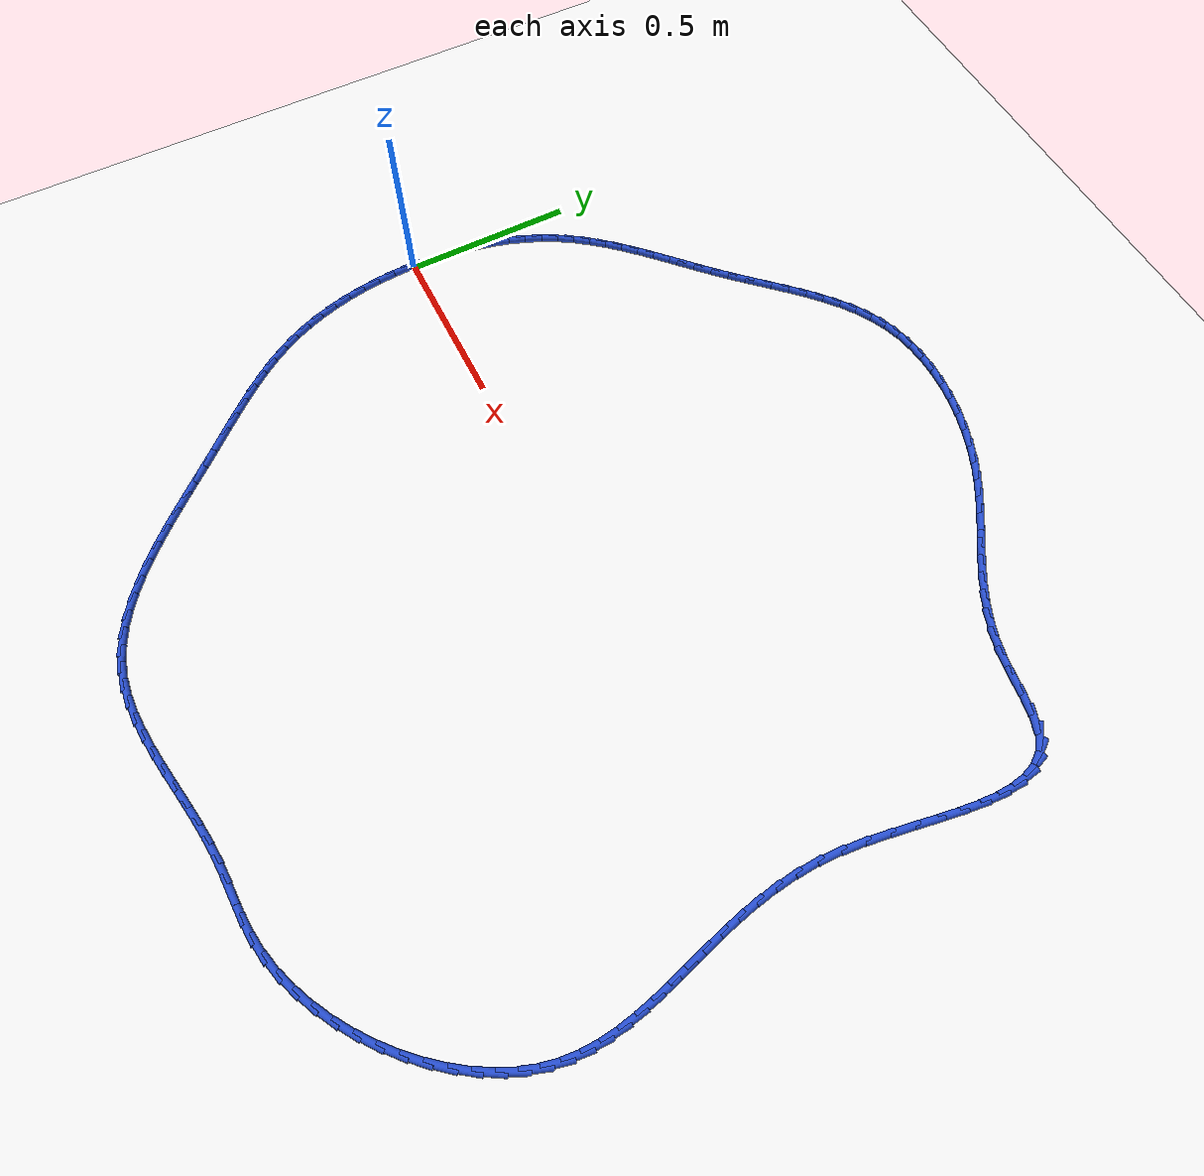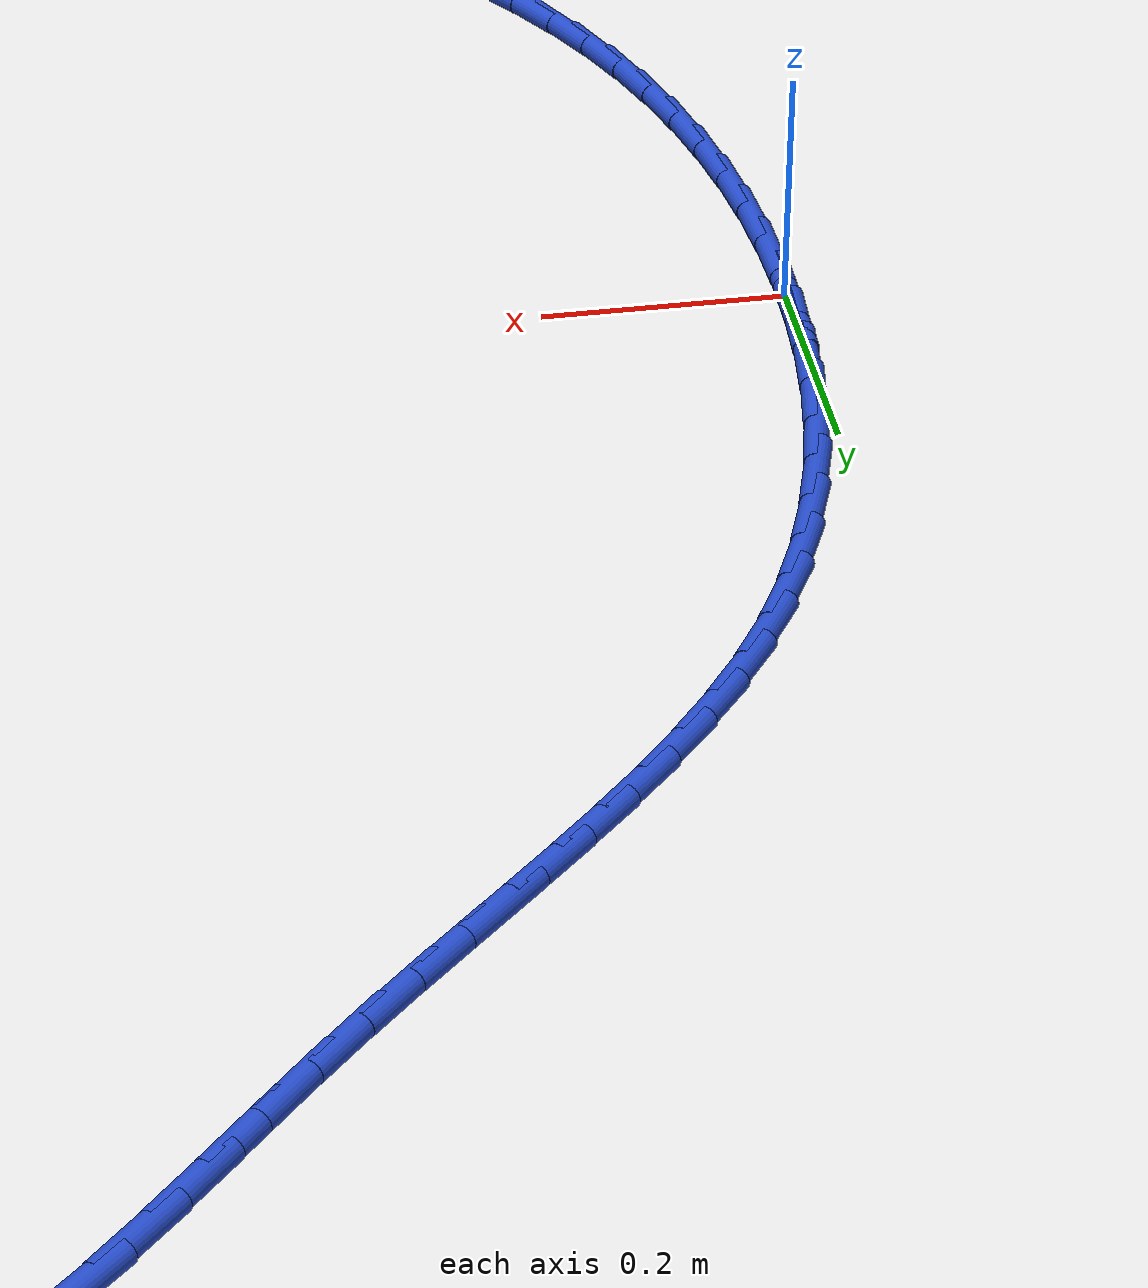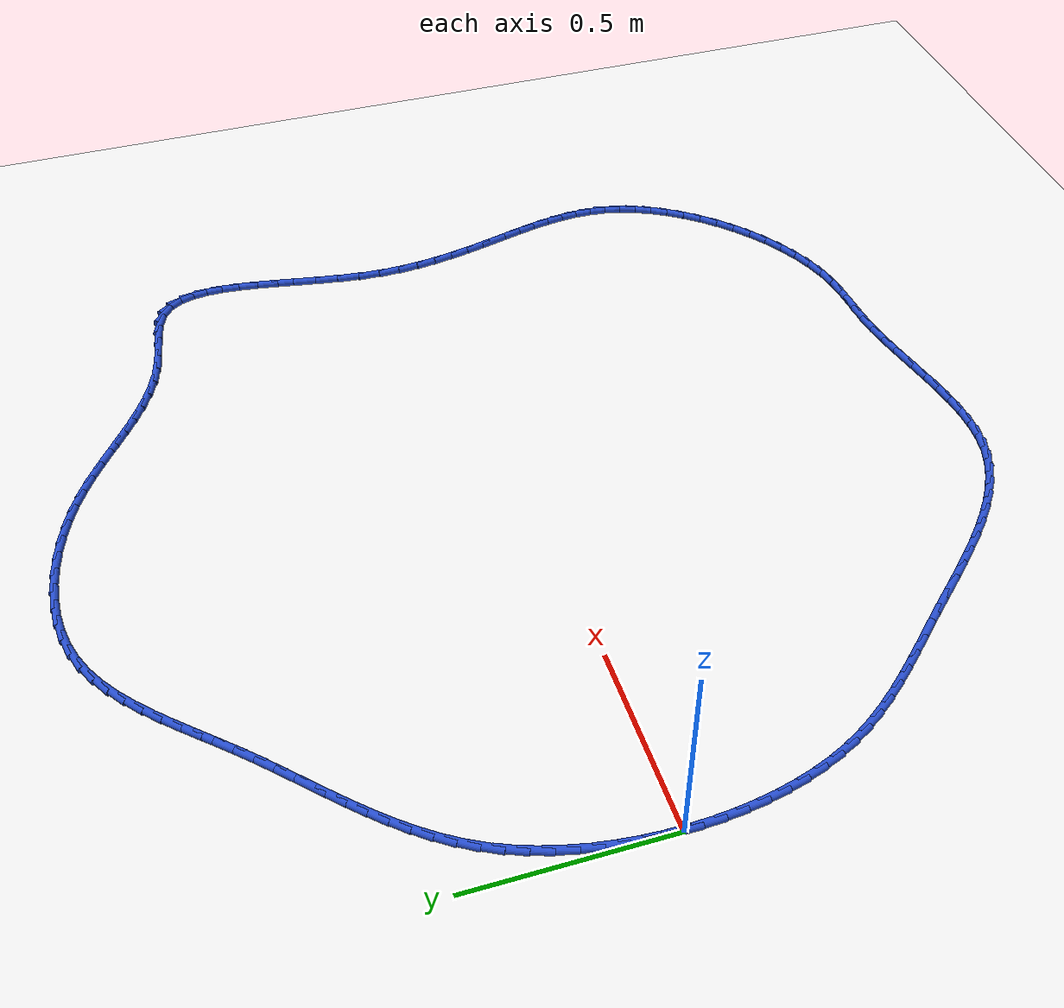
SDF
<sdf version="1.6">
 <world name="default">
  <light name="sun" type="directional">
   <pose>0 0 10 0 -0 0</pose>
   <diffuse>0.8 0.8 0.8 1</diffuse>
   <specular>0.2 0.2 0.2 1</specular>
   <attenuation>
    <range>1000</range>
    <constant>0.9</constant>
    <linear>0.01</linear>
    <quadratic>0.001</quadratic>
   </attenuation>
   <direction>-0.5 0.1 -0.9</direction>
  </light>
  <model name="ground_plane">
   <static>1</static>
   <link name="link">
    <collision name="collision">
     <geometry><plane><normal>0 0 1</normal><size>100 100</size></plane></geometry>
     <surface><friction><ode><mu>100</mu><mu2>50</mu2></ode></friction></surface>
    </collision>
    <visual name="visual">
     <cast_shadows>0</cast_shadows>
     <geometry><plane><normal>0 0 1</normal><size>100 100</size></plane></geometry>
     <material>
      <script><uri>file://media/materials/scripts/gazebo.material</uri><name>Gazebo/WhiteGlow</name></script>
     </material>
    </visual>
   </link>
  </model>
  <gravity>0 0 -9.8</gravity>
  <magnetic_field>6e-06 2.3e-05 -4.2e-05</magnetic_field>
  <atmosphere type="adiabatic"/>
  <physics name="default_physics" default="0" type="ode">
   <max_step_size>0.001</max_step_size>
   <real_time_factor>1</real_time_factor>
   <real_time_update_rate>1000</real_time_update_rate>
  </physics>
  <scene><ambient>0.4 0.4 0.4 1</ambient><background>0.7 0.7 0.7 1</background><shadows>1</shadows></scene>
  <spherical_coordinates>
   <surface_model>EARTH_WGS84</surface_model>
   <latitude_deg>0</latitude_deg>
   <longitude_deg>0</longitude_deg>
   <elevation>0</elevation>
   <heading_deg>0</heading_deg>
  </spherical_coordinates>
  <model name="line">
   <link name="link_0">
    <pose>-3.122502256758253e-17 -2.7755575615628914e-17 0.01 0 1.57 1.5520226301388294</pose>
    <collision name="collision">
     <geometry><cylinder><radius>0.01</radius><length>0.08</length></cylinder></geometry>
    </collision>
    <visual name="visual">
     <material>
      <script><name>Gazebo/Blue</name><uri>file://media/materials/scripts/gazebo.material</uri></script>
     </material>
     <geometry><cylinder><radius>0.01</radius><length>0.08</length></cylinder></geometry>
    </visual>
   </link>
   <link name="link_1">
    <pose>0.0010015984255238716 0.05334488829884319 0.01 0 1.57 1.504426610533225</pose>
    <collision name="collision">
     <geometry><cylinder><radius>0.01</radius><length>0.08</length></cylinder></geometry>
    </collision>
    <visual name="visual">
     <material>
      <script><name>Gazebo/Blue</name><uri>file://media/materials/scripts/gazebo.material</uri></script>
     </material>
     <geometry><cylinder><radius>0.01</radius><length>0.08</length></cylinder></geometry>
    </visual>
   </link>
   <link name="link_2">
    <pose>0.004533960083231481 0.10648920953153208 0.01 0 1.57 1.4543161858426692</pose>
    <collision name="collision">
     <geometry><cylinder><radius>0.01</radius><length>0.08</length></cylinder></geometry>
    </collision>
    <visual name="visual">
     <material>
      <script><name>Gazebo/Blue</name><uri>file://media/materials/scripts/gazebo.material</uri></script>
     </material>
     <geometry><cylinder><radius>0.01</radius><length>0.08</length></cylinder></geometry>
    </visual>
   </link>
   <link name="link_3">
    <pose>0.010697657855469344 0.15916597399450033 0.01 0 1.57 1.4011821433536542</pose>
    <collision name="collision">
     <geometry><cylinder><radius>0.01</radius><length>0.08</length></cylinder></geometry>
    </collision>
    <visual name="visual">
     <material>
      <script><name>Gazebo/Blue</name><uri>file://media/materials/scripts/gazebo.material</uri></script>
     </material>
     <geometry><cylinder><radius>0.01</radius><length>0.08</length></cylinder></geometry>
    </visual>
   </link>
   <link name="link_4">
    <pose>0.019593264624583995 0.21110819198418143 0.01 0 1.57 1.3445092169974802</pose>
    <collision name="collision">
     <geometry><cylinder><radius>0.01</radius><length>0.08</length></cylinder></geometry>
    </collision>
    <visual name="visual">
     <material>
      <script><name>Gazebo/Blue</name><uri>file://media/materials/scripts/gazebo.material</uri></script>
     </material>
     <geometry><cylinder><radius>0.01</radius><length>0.08</length></cylinder></geometry>
    </visual>
   </link>
   <link name="link_5">
    <pose>0.03132135327292199 0.2620488737970091 0.01 0 1.57 1.2837874621200238</pose>
    <collision name="collision">
     <geometry><cylinder><radius>0.01</radius><length>0.08</length></cylinder></geometry>
    </collision>
    <visual name="visual">
     <material>
      <script><name>Gazebo/Blue</name><uri>file://media/materials/scripts/gazebo.material</uri></script>
     </material>
     <geometry><cylinder><radius>0.01</radius><length>0.08</length></cylinder></geometry>
    </visual>
   </link>
   <link name="link_6">
    <pose>0.045982496682829846 0.31172102972941673 0.01 0 1.57 1.2185337788464226</pose>
    <collision name="collision">
     <geometry><cylinder><radius>0.01</radius><length>0.08</length></cylinder></geometry>
    </collision>
    <visual name="visual">
     <material>
      <script><name>Gazebo/Blue</name><uri>file://media/materials/scripts/gazebo.material</uri></script>
     </material>
     <geometry><cylinder><radius>0.01</radius><length>0.08</length></cylinder></geometry>
    </visual>
   </link>
   <link name="link_7">
    <pose>0.06367726773665412 0.3598576700778381 0.01 0 1.57 1.1483263583352719</pose>
    <collision name="collision">
     <geometry><cylinder><radius>0.01</radius><length>0.08</length></cylinder></geometry>
    </collision>
    <visual name="visual">
     <material>
      <script><name>Gazebo/Blue</name><uri>file://media/materials/scripts/gazebo.material</uri></script>
     </material>
     <geometry><cylinder><radius>0.01</radius><length>0.08</length></cylinder></geometry>
    </visual>
   </link>
   <link name="link_8">
    <pose>0.08450623931674137 0.4061918051387067 0.01 0 1.57 1.0729823649552666</pose>
    <collision name="collision">
     <geometry><cylinder><radius>0.01</radius><length>0.08</length></cylinder></geometry>
    </collision>
    <visual name="visual">
     <material>
      <script><name>Gazebo/Blue</name><uri>file://media/materials/scripts/gazebo.material</uri></script>
     </material>
     <geometry><cylinder><radius>0.01</radius><length>0.08</length></cylinder></geometry>
    </visual>
   </link>
   <link name="link_9">
    <pose>0.10856555104489769 0.45046182197065393 0.01 0 1.57 0.9981862404198574</pose>
    <collision name="collision">
     <geometry><cylinder><radius>0.01</radius><length>0.08</length></cylinder></geometry>
    </collision>
    <visual name="visual">
     <material>
      <script><name>Gazebo/Blue</name><uri>file://media/materials/scripts/gazebo.material</uri></script>
     </material>
     <geometry><cylinder><radius>0.01</radius><length>0.08</length></cylinder></geometry>
    </visual>
   </link>
   <link name="link_10">
    <pose>0.1357571023206065 0.49264168672250913 0.01 0 1.57 0.9325389733299151</pose>
    <collision name="collision">
     <geometry><cylinder><radius>0.01</radius><length>0.08</length></cylinder></geometry>
    </collision>
    <visual name="visual">
     <material>
      <script><name>Gazebo/Blue</name><uri>file://media/materials/scripts/gazebo.material</uri></script>
     </material>
     <geometry><cylinder><radius>0.01</radius><length>0.08</length></cylinder></geometry>
    </visual>
   </link>
   <link name="link_11">
    <pose>0.1657170139983342 0.5330277079862896 0.01 0 1.57 0.8772916254785371</pose>
    <collision name="collision">
     <geometry><cylinder><radius>0.01</radius><length>0.08</length></cylinder></geometry>
    </collision>
    <visual name="visual">
     <material>
      <script><name>Gazebo/Blue</name><uri>file://media/materials/scripts/gazebo.material</uri></script>
     </material>
     <geometry><cylinder><radius>0.01</radius><length>0.08</length></cylinder></geometry>
    </visual>
   </link>
   <link name="link_12">
    <pose>0.1980622235505943 0.5719394604088672 0.01 0 1.57 0.8326500714863959</pose>
    <collision name="collision">
     <geometry><cylinder><radius>0.01</radius><length>0.08</length></cylinder></geometry>
    </collision>
    <visual name="visual">
     <material>
      <script><name>Gazebo/Blue</name><uri>file://media/materials/scripts/gazebo.material</uri></script>
     </material>
     <geometry><cylinder><radius>0.01</radius><length>0.08</length></cylinder></geometry>
    </visual>
   </link>
   <link name="link_13">
    <pose>0.23240966844990016 0.6096965186371133 0.01 0 1.57 0.7985040103526376</pose>
    <collision name="collision">
     <geometry><cylinder><radius>0.01</radius><length>0.08</length></cylinder></geometry>
    </collision>
    <visual name="visual">
     <material>
      <script><name>Gazebo/Blue</name><uri>file://media/materials/scripts/gazebo.material</uri></script>
     </material>
     <geometry><cylinder><radius>0.01</radius><length>0.08</length></cylinder></geometry>
    </visual>
   </link>
   <link name="link_14">
    <pose>0.26837628616876535 0.6466184573178996 0.01 0 1.57 0.7745801676602412</pose>
    <collision name="collision">
     <geometry><cylinder><radius>0.01</radius><length>0.08</length></cylinder></geometry>
    </collision>
    <visual name="visual">
     <material>
      <script><name>Gazebo/Blue</name><uri>file://media/materials/scripts/gazebo.material</uri></script>
     </material>
     <geometry><cylinder><radius>0.01</radius><length>0.08</length></cylinder></geometry>
    </visual>
   </link>
   <link name="link_15">
    <pose>0.3055790141797033 0.6830248510980977 0.01 0 1.57 0.7605554674579768</pose>
    <collision name="collision">
     <geometry><cylinder><radius>0.01</radius><length>0.08</length></cylinder></geometry>
    </collision>
    <visual name="visual">
     <material>
      <script><name>Gazebo/Blue</name><uri>file://media/materials/scripts/gazebo.material</uri></script>
     </material>
     <geometry><cylinder><radius>0.01</radius><length>0.08</length></cylinder></geometry>
    </visual>
   </link>
   <link name="link_16">
    <pose>0.3436347899552275 0.7192352746245791 0.01 0 1.57 0.7561286824018808</pose>
    <collision name="collision">
     <geometry><cylinder><radius>0.01</radius><length>0.08</length></cylinder></geometry>
    </collision>
    <visual name="visual">
     <material>
      <script><name>Gazebo/Blue</name><uri>file://media/materials/scripts/gazebo.material</uri></script>
     </material>
     <geometry><cylinder><radius>0.01</radius><length>0.08</length></cylinder></geometry>
    </visual>
   </link>
   <link name="link_17">
    <pose>0.3821605509678513 0.7555693025442154 0.01 0 1.57 0.7610565147322137</pose>
    <collision name="collision">
     <geometry><cylinder><radius>0.01</radius><length>0.08</length></cylinder></geometry>
    </collision>
    <visual name="visual">
     <material>
      <script><name>Gazebo/Blue</name><uri>file://media/materials/scripts/gazebo.material</uri></script>
     </material>
     <geometry><cylinder><radius>0.01</radius><length>0.08</length></cylinder></geometry>
    </visual>
   </link>
   <link name="link_18">
    <pose>0.42077323469008815 0.7923465095038784 0.01 0 1.57 0.7751609908089492</pose>
    <collision name="collision">
     <geometry><cylinder><radius>0.01</radius><length>0.08</length></cylinder></geometry>
    </collision>
    <visual name="visual">
     <material>
      <script><name>Gazebo/Blue</name><uri>file://media/materials/scripts/gazebo.material</uri></script>
     </material>
     <geometry><cylinder><radius>0.01</radius><length>0.08</length></cylinder></geometry>
    </visual>
   </link>
   <link name="link_19">
    <pose>0.45908977859445166 0.8298864701504395 0.01 0 1.57 0.7971833803515097</pose>
    <collision name="collision">
     <geometry><cylinder><radius>0.01</radius><length>0.08</length></cylinder></geometry>
    </collision>
    <visual name="visual">
     <material>
      <script><name>Gazebo/Blue</name><uri>file://media/materials/scripts/gazebo.material</uri></script>
     </material>
     <geometry><cylinder><radius>0.01</radius><length>0.08</length></cylinder></geometry>
    </visual>
   </link>
   <link name="link_20">
    <pose>0.4967634171352675 0.8684587246867367 0.01 0 1.57 0.8139270701190434</pose>
    <collision name="collision">
     <geometry><cylinder><radius>0.01</radius><length>0.08</length></cylinder></geometry>
    </collision>
    <visual name="visual">
     <material>
      <script><name>Gazebo/Blue</name><uri>file://media/materials/scripts/gazebo.material</uri></script>
     </material>
     <geometry><cylinder><radius>0.01</radius><length>0.08</length></cylinder></geometry>
    </visual>
   </link>
   <link name="link_21">
    <pose>0.533872025485427 0.9077474571452956 0.01 0 1.57 0.8170551658994607</pose>
    <collision name="collision">
     <geometry><cylinder><radius>0.01</radius><length>0.08</length></cylinder></geometry>
    </collision>
    <visual name="visual">
     <material>
      <script><name>Gazebo/Blue</name><uri>file://media/materials/scripts/gazebo.material</uri></script>
     </material>
     <geometry><cylinder><radius>0.01</radius><length>0.08</length></cylinder></geometry>
    </visual>
   </link>
   <link name="link_22">
    <pose>0.5707687225092505 0.9470574352990285 0.01 0 1.57 0.8063676466165471</pose>
    <collision name="collision">
     <geometry><cylinder><radius>0.01</radius><length>0.08</length></cylinder></geometry>
    </collision>
    <visual name="visual">
     <material>
      <script><name>Gazebo/Blue</name><uri>file://media/materials/scripts/gazebo.material</uri></script>
     </material>
     <geometry><cylinder><radius>0.01</radius><length>0.08</length></cylinder></geometry>
    </visual>
   </link>
   <link name="link_23">
    <pose>0.6078112724056012 0.9856870234481746 0.01 0 1.57 0.7814058108458038</pose>
    <collision name="collision">
     <geometry><cylinder><radius>0.01</radius><length>0.08</length></cylinder></geometry>
    </collision>
    <visual name="visual">
     <material>
      <script><name>Gazebo/Blue</name><uri>file://media/materials/scripts/gazebo.material</uri></script>
     </material>
     <geometry><cylinder><radius>0.01</radius><length>0.08</length></cylinder></geometry>
    </visual>
   </link>
   <link name="link_24">
    <pose>0.6453574393733413 1.0229345858929721 0.01 0 1.57 0.7413383001752649</pose>
    <collision name="collision">
     <geometry><cylinder><radius>0.01</radius><length>0.08</length></cylinder></geometry>
    </collision>
    <visual name="visual">
     <material>
      <script><name>Gazebo/Blue</name><uri>file://media/materials/scripts/gazebo.material</uri></script>
     </material>
     <geometry><cylinder><radius>0.01</radius><length>0.08</length></cylinder></geometry>
    </visual>
   </link>
   <link name="link_25">
    <pose>0.6837649876113341 1.0580984869336605 0.01 0 1.57 0.6850755863992588</pose>
    <collision name="collision">
     <geometry><cylinder><radius>0.01</radius><length>0.08</length></cylinder></geometry>
    </collision>
    <visual name="visual">
     <material>
      <script><name>Gazebo/Blue</name><uri>file://media/materials/scripts/gazebo.material</uri></script>
     </material>
     <geometry><cylinder><radius>0.01</radius><length>0.08</length></cylinder></geometry>
    </visual>
   </link>
   <link name="link_26">
    <pose>0.7233916813184419 1.0904770908704784 0.01 0 1.57 0.6115260708818135</pose>
    <collision name="collision">
     <geometry><cylinder><radius>0.01</radius><length>0.08</length></cylinder></geometry>
    </collision>
    <visual name="visual">
     <material>
      <script><name>Gazebo/Blue</name><uri>file://media/materials/scripts/gazebo.material</uri></script>
     </material>
     <geometry><cylinder><radius>0.01</radius><length>0.08</length></cylinder></geometry>
    </visual>
   </link>
   <link name="link_27">
    <pose>0.7645952846935277 1.1193687620036645 0.01 0 1.57 0.5200658433095797</pose>
    <collision name="collision">
     <geometry><cylinder><radius>0.01</radius><length>0.08</length></cylinder></geometry>
    </collision>
    <visual name="visual">
     <material>
      <script><name>Gazebo/Blue</name><uri>file://media/materials/scripts/gazebo.material</uri></script>
     </material>
     <geometry><cylinder><radius>0.01</radius><length>0.08</length></cylinder></geometry>
    </visual>
   </link>
   <link name="link_28">
    <pose>0.8077335619354542 1.144071864633458 0.01 0 1.57 0.41124757124227806</pose>
    <collision name="collision">
     <geometry><cylinder><radius>0.01</radius><length>0.08</length></cylinder></geometry>
    </collision>
    <visual name="visual">
     <material>
      <script><name>Gazebo/Blue</name><uri>file://media/materials/scripts/gazebo.material</uri></script>
     </material>
     <geometry><cylinder><radius>0.01</radius><length>0.08</length></cylinder></geometry>
    </visual>
   </link>
   <link name="link_29">
    <pose>0.8531641958488091 1.163884857030394 0.01 0 1.57 0.2925708995511331</pose>
    <collision name="collision">
     <geometry><cylinder><radius>0.01</radius><length>0.08</length></cylinder></geometry>
    </collision>
    <visual name="visual">
     <material>
      <script><name>Gazebo/Blue</name><uri>file://media/materials/scripts/gazebo.material</uri></script>
     </material>
     <geometry><cylinder><radius>0.01</radius><length>0.08</length></cylinder></geometry>
    </visual>
   </link>
   <link name="link_30">
    <pose>0.9010653919522748 1.1783134053267605 0.01 0 1.57 0.18193671779590934</pose>
    <collision name="collision">
     <geometry><cylinder><radius>0.01</radius><length>0.08</length></cylinder></geometry>
    </collision>
    <visual name="visual">
     <material>
      <script><name>Gazebo/Blue</name><uri>file://media/materials/scripts/gazebo.material</uri></script>
     </material>
     <geometry><cylinder><radius>0.01</radius><length>0.08</length></cylinder></geometry>
    </visual>
   </link>
   <link name="link_31">
    <pose>0.9510550469120987 1.187510056393263 0.01 0 1.57 0.082068290474692</pose>
    <collision name="collision">
     <geometry><cylinder><radius>0.01</radius><length>0.08</length></cylinder></geometry>
    </collision>
    <visual name="visual">
     <material>
      <script><name>Gazebo/Blue</name><uri>file://media/materials/scripts/gazebo.material</uri></script>
     </material>
     <geometry><cylinder><radius>0.01</radius><length>0.08</length></cylinder></geometry>
    </visual>
   </link>
   <link name="link_32">
    <pose>1.0026420199825927 1.19175324160384 0.01 0 1.57 -0.008195365043716402</pose>
    <collision name="collision">
     <geometry><cylinder><radius>0.01</radius><length>0.08</length></cylinder></geometry>
    </collision>
    <visual name="visual">
     <material>
      <script><name>Gazebo/Blue</name><uri>file://media/materials/scripts/gazebo.material</uri></script>
     </material>
     <geometry><cylinder><radius>0.01</radius><length>0.08</length></cylinder></geometry>
    </visual>
   </link>
   <link name="link_33">
    <pose>1.0553351704180698 1.191321392332432 0.01 0 1.57 -0.09032970323256534</pose>
    <collision name="collision">
     <geometry><cylinder><radius>0.01</radius><length>0.08</length></cylinder></geometry>
    </collision>
    <visual name="visual">
     <material>
      <script><name>Gazebo/Blue</name><uri>file://media/materials/scripts/gazebo.material</uri></script>
     </material>
     <geometry><cylinder><radius>0.01</radius><length>0.08</length></cylinder></geometry>
    </visual>
   </link>
   <link name="link_34">
    <pose>1.108643357472842 1.1864929399529782 0.01 0 1.57 -0.16590021703483696</pose>
    <collision name="collision">
     <geometry><cylinder><radius>0.01</radius><length>0.08</length></cylinder></geometry>
    </collision>
    <visual name="visual">
     <material>
      <script><name>Gazebo/Blue</name><uri>file://media/materials/scripts/gazebo.material</uri></script>
     </material>
     <geometry><cylinder><radius>0.01</radius><length>0.08</length></cylinder></geometry>
    </visual>
   </link>
   <link name="link_35">
    <pose>1.1620754404012217 1.177546315839418 0.01 0 1.57 -0.23645002435855425</pose>
    <collision name="collision">
     <geometry><cylinder><radius>0.01</radius><length>0.08</length></cylinder></geometry>
    </collision>
    <visual name="visual">
     <material>
      <script><name>Gazebo/Blue</name><uri>file://media/materials/scripts/gazebo.material</uri></script>
     </material>
     <geometry><cylinder><radius>0.01</radius><length>0.08</length></cylinder></geometry>
    </visual>
   </link>
   <link name="link_36">
    <pose>1.215140278457521 1.1647599513656912 0.01 0 1.57 -0.3034633733236827</pose>
    <collision name="collision">
     <geometry><cylinder><radius>0.01</radius><length>0.08</length></cylinder></geometry>
    </collision>
    <visual name="visual">
     <material>
      <script><name>Gazebo/Blue</name><uri>file://media/materials/scripts/gazebo.material</uri></script>
     </material>
     <geometry><cylinder><radius>0.01</radius><length>0.08</length></cylinder></geometry>
    </visual>
   </link>
   <link name="link_37">
    <pose>1.2673467308960529 1.1484122779057369 0.01 0 1.57 -0.3683756536316229</pose>
    <collision name="collision">
     <geometry><cylinder><radius>0.01</radius><length>0.08</length></cylinder></geometry>
    </collision>
    <visual name="visual">
     <material>
      <script><name>Gazebo/Blue</name><uri>file://media/materials/scripts/gazebo.material</uri></script>
     </material>
     <geometry><cylinder><radius>0.01</radius><length>0.08</length></cylinder></geometry>
    </visual>
   </link>
   <link name="link_38">
    <pose>1.318203656971129 1.1287817268334956 0.01 0 1.57 -0.43261140673777254</pose>
    <collision name="collision">
     <geometry><cylinder><radius>0.01</radius><length>0.08</length></cylinder></geometry>
    </collision>
    <visual name="visual">
     <material>
      <script><name>Gazebo/Blue</name><uri>file://media/materials/scripts/gazebo.material</uri></script>
     </material>
     <geometry><cylinder><radius>0.01</radius><length>0.08</length></cylinder></geometry>
    </visual>
   </link>
   <link name="link_39">
    <pose>1.3672199159370626 1.1061467295229064 0.01 0 1.57 -0.4964022953767984</pose>
    <collision name="collision">
     <geometry><cylinder><radius>0.01</radius><length>0.08</length></cylinder></geometry>
    </collision>
    <visual name="visual">
     <material>
      <script><name>Gazebo/Blue</name><uri>file://media/materials/scripts/gazebo.material</uri></script>
     </material>
     <geometry><cylinder><radius>0.01</radius><length>0.08</length></cylinder></geometry>
    </visual>
   </link>
   <link name="link_40">
    <pose>1.4139813918026618 1.0808188340793081 0.01 0 1.57 -0.5498269317807943</pose>
    <collision name="collision">
     <geometry><cylinder><radius>0.01</radius><length>0.08</length></cylinder></geometry>
    </collision>
    <visual name="visual">
     <material>
      <script><name>Gazebo/Blue</name><uri>file://media/materials/scripts/gazebo.material</uri></script>
     </material>
     <geometry><cylinder><radius>0.01</radius><length>0.08</length></cylinder></geometry>
    </visual>
   </link>
   <link name="link_41">
    <pose>1.458732143149102 1.0533925702373774 0.01 0 1.57 -0.5865311515154973</pose>
    <collision name="collision">
     <geometry><cylinder><radius>0.01</radius><length>0.08</length></cylinder></geometry>
    </collision>
    <visual name="visual">
     <material>
      <script><name>Gazebo/Blue</name><uri>file://media/materials/scripts/gazebo.material</uri></script>
     </material>
     <geometry><cylinder><radius>0.01</radius><length>0.08</length></cylinder></geometry>
    </visual>
   </link>
   <link name="link_42">
    <pose>1.5020500049786678 1.0246059746362601 0.01 0 1.57 -0.6056820950176903</pose>
    <collision name="collision">
     <geometry><cylinder><radius>0.01</radius><length>0.08</length></cylinder></geometry>
    </collision>
    <visual name="visual">
     <material>
      <script><name>Gazebo/Blue</name><uri>file://media/materials/scripts/gazebo.material</uri></script>
     </material>
     <geometry><cylinder><radius>0.01</radius><length>0.08</length></cylinder></geometry>
    </visual>
   </link>
   <link name="link_43">
    <pose>1.5445154217681598 0.9951982058565767 0.01 0 1.57 -0.6068085583690379</pose>
    <collision name="collision">
     <geometry><cylinder><radius>0.01</radius><length>0.08</length></cylinder></geometry>
    </collision>
    <visual name="visual">
     <material>
      <script><name>Gazebo/Blue</name><uri>file://media/materials/scripts/gazebo.material</uri></script>
     </material>
     <geometry><cylinder><radius>0.01</radius><length>0.08</length></cylinder></geometry>
    </visual>
   </link>
   <link name="link_44">
    <pose>1.5867088379943783 0.9659084224789467 0.01 0 1.57 -0.5895982876862703</pose>
    <collision name="collision">
     <geometry><cylinder><radius>0.01</radius><length>0.08</length></cylinder></geometry>
    </collision>
    <visual name="visual">
     <material>
      <script><name>Gazebo/Blue</name><uri>file://media/materials/scripts/gazebo.material</uri></script>
     </material>
     <geometry><cylinder><radius>0.01</radius><length>0.08</length></cylinder></geometry>
    </visual>
   </link>
   <link name="link_45">
    <pose>1.6292106981341241 0.937475783083991 0.01 0 1.57 -0.5538974760623594</pose>
    <collision name="collision">
     <geometry><cylinder><radius>0.01</radius><length>0.08</length></cylinder></geometry>
    </collision>
    <visual name="visual">
     <material>
      <script><name>Gazebo/Blue</name><uri>file://media/materials/scripts/gazebo.material</uri></script>
     </material>
     <geometry><cylinder><radius>0.01</radius><length>0.08</length></cylinder></geometry>
    </visual>
   </link>
   <link name="link_46">
    <pose>1.6726014466641979 0.9106394462523294 0.01 0 1.57 -0.4998918623525935</pose>
    <collision name="collision">
     <geometry><cylinder><radius>0.01</radius><length>0.08</length></cylinder></geometry>
    </collision>
    <visual name="visual">
     <material>
      <script><name>Gazebo/Blue</name><uri>file://media/materials/scripts/gazebo.material</uri></script>
     </material>
     <geometry><cylinder><radius>0.01</radius><length>0.08</length></cylinder></geometry>
    </visual>
   </link>
   <link name="link_47">
    <pose>1.7174615280613992 0.8861385705645821 0.01 0 1.57 -0.42845616905940254</pose>
    <collision name="collision">
     <geometry><cylinder><radius>0.01</radius><length>0.08</length></cylinder></geometry>
    </collision>
    <visual name="visual">
     <material>
      <script><name>Gazebo/Blue</name><uri>file://media/materials/scripts/gazebo.material</uri></script>
     </material>
     <geometry><cylinder><radius>0.01</radius><length>0.08</length></cylinder></geometry>
    </visual>
   </link>
   <link name="link_48">
    <pose>1.76437138680253 0.8647123146013692 0.01 0 1.57 -0.3415837140266836</pose>
    <collision name="collision">
     <geometry><cylinder><radius>0.01</radius><length>0.08</length></cylinder></geometry>
    </collision>
    <visual name="visual">
     <material>
      <script><name>Gazebo/Blue</name><uri>file://media/materials/scripts/gazebo.material</uri></script>
     </material>
     <geometry><cylinder><radius>0.01</radius><length>0.08</length></cylinder></geometry>
    </visual>
   </link>
   <link name="link_49">
    <pose>1.8139114673643901 0.8470998369433116 0.01 0 1.57 -0.2432140804673732</pose>
    <collision name="collision">
     <geometry><cylinder><radius>0.01</radius><length>0.08</length></cylinder></geometry>
    </collision>
    <visual name="visual">
     <material>
      <script><name>Gazebo/Blue</name><uri>file://media/materials/scripts/gazebo.material</uri></script>
     </material>
     <geometry><cylinder><radius>0.01</radius><length>0.08</length></cylinder></geometry>
    </visual>
   </link>
   <link name="link_50">
    <pose>1.866638337552057 0.8340169318866262 0.01 0 1.57 -0.166882925361371</pose>
    <collision name="collision">
     <geometry><cylinder><radius>0.01</radius><length>0.08</length></cylinder></geometry>
    </collision>
    <visual name="visual">
     <material>
      <script><name>Gazebo/Blue</name><uri>file://media/materials/scripts/gazebo.material</uri></script>
     </material>
     <geometry><cylinder><radius>0.01</radius><length>0.08</length></cylinder></geometry>
    </visual>
   </link>
   <link name="link_51">
    <pose>1.9216483522651584 0.8247505166207728 0.01 0 1.57 -0.15389126715999707</pose>
    <collision name="collision">
     <geometry><cylinder><radius>0.01</radius><length>0.08</length></cylinder></geometry>
    </collision>
    <visual name="visual">
     <material>
      <script><name>Gazebo/Blue</name><uri>file://media/materials/scripts/gazebo.material</uri></script>
     </material>
     <geometry><cylinder><radius>0.01</radius><length>0.08</length></cylinder></geometry>
    </visual>
   </link>
   <link name="link_52">
    <pose>1.9757585147408832 0.8163570709814785 0.01 0 1.57 -0.21070930052542367</pose>
    <collision name="collision">
     <geometry><cylinder><radius>0.01</radius><length>0.08</length></cylinder></geometry>
    </collision>
    <visual name="visual">
     <material>
      <script><name>Gazebo/Blue</name><uri>file://media/materials/scripts/gazebo.material</uri></script>
     </material>
     <geometry><cylinder><radius>0.01</radius><length>0.08</length></cylinder></geometry>
    </visual>
   </link>
   <link name="link_53">
    <pose>2.0255878703610293 0.8056993650744643 0.01 0 1.57 -0.36388266815558895</pose>
    <collision name="collision">
     <geometry><cylinder><radius>0.01</radius><length>0.08</length></cylinder></geometry>
    </collision>
    <visual name="visual">
     <material>
      <script><name>Gazebo/Blue</name><uri>file://media/materials/scripts/gazebo.material</uri></script>
     </material>
     <geometry><cylinder><radius>0.01</radius><length>0.08</length></cylinder></geometry>
    </visual>
   </link>
   <link name="link_54">
    <pose>2.067755464507398 0.7896401690054519 0.01 0 1.57 -0.6471197565963764</pose>
    <collision name="collision">
     <geometry><cylinder><radius>0.01</radius><length>0.08</length></cylinder></geometry>
    </collision>
    <visual name="visual">
     <material>
      <script><name>Gazebo/Blue</name><uri>file://media/materials/scripts/gazebo.material</uri></script>
     </material>
     <geometry><cylinder><radius>0.01</radius><length>0.08</length></cylinder></geometry>
    </visual>
   </link>
   <link name="link_55">
    <pose>2.0995490879622016 0.7656146959078071 0.01 0 1.57 -0.9707340508960112</pose>
    <collision name="collision">
     <geometry><cylinder><radius>0.01</radius><length>0.08</length></cylinder></geometry>
    </collision>
    <visual name="visual">
     <material>
      <script><name>Gazebo/Blue</name><uri>file://media/materials/scripts/gazebo.material</uri></script>
     </material>
     <geometry><cylinder><radius>0.01</radius><length>0.08</length></cylinder></geometry>
    </visual>
   </link>
   <link name="link_56">
    <pose>2.1213700627127334 0.7337233274956491 0.01 0 1.57 -1.2445515457175276</pose>
    <collision name="collision">
     <geometry><cylinder><radius>0.01</radius><length>0.08</length></cylinder></geometry>
    </collision>
    <visual name="visual">
     <material>
      <script><name>Gazebo/Blue</name><uri>file://media/materials/scripts/gazebo.material</uri></script>
     </material>
     <geometry><cylinder><radius>0.01</radius><length>0.08</length></cylinder></geometry>
    </visual>
   </link>
   <link name="link_57">
    <pose>2.134525130690281 0.6948414808458958 0.01 0 1.57 -1.4426925245071953</pose>
    <collision name="collision">
     <geometry><cylinder><radius>0.01</radius><length>0.08</length></cylinder></geometry>
    </collision>
    <visual name="visual">
     <material>
      <script><name>Gazebo/Blue</name><uri>file://media/materials/scripts/gazebo.material</uri></script>
     </material>
     <geometry><cylinder><radius>0.01</radius><length>0.08</length></cylinder></geometry>
    </visual>
   </link>
   <link name="link_58">
    <pose>2.1403211346295112 0.6498446593227035 0.01 0 1.57 1.5656961267727911</pose>
    <collision name="collision">
     <geometry><cylinder><radius>0.01</radius><length>0.08</length></cylinder></geometry>
    </collision>
    <visual name="visual">
     <material>
      <script><name>Gazebo/Blue</name><uri>file://media/materials/scripts/gazebo.material</uri></script>
     </material>
     <geometry><cylinder><radius>0.01</radius><length>0.08</length></cylinder></geometry>
    </visual>
   </link>
   <link name="link_59">
    <pose>2.140064917265094 0.5996083662902271 0.01 0 1.57 1.4794473858550248</pose>
    <collision name="collision">
     <geometry><cylinder><radius>0.01</radius><length>0.08</length></cylinder></geometry>
    </collision>
    <visual name="visual">
     <material>
      <script><name>Gazebo/Blue</name><uri>file://media/materials/scripts/gazebo.material</uri></script>
     </material>
     <geometry><cylinder><radius>0.01</radius><length>0.08</length></cylinder></geometry>
    </visual>
   </link>
   <link name="link_60">
    <pose>2.135063321331697 0.5450081051126229 0.01 0 1.57 1.4265087946099895</pose>
    <collision name="collision">
     <geometry><cylinder><radius>0.01</radius><length>0.08</length></cylinder></geometry>
    </collision>
    <visual name="visual">
     <material>
      <script><name>Gazebo/Blue</name><uri>file://media/materials/scripts/gazebo.material</uri></script>
     </material>
     <geometry><cylinder><radius>0.01</radius><length>0.08</length></cylinder></geometry>
    </visual>
   </link>
   <link name="link_61">
    <pose>2.126623189563988 0.48691937915404554 0.01 0 1.57 1.398365512150488</pose>
    <collision name="collision">
     <geometry><cylinder><radius>0.01</radius><length>0.08</length></cylinder></geometry>
    </collision>
    <visual name="visual">
     <material>
      <script><name>Gazebo/Blue</name><uri>file://media/materials/scripts/gazebo.material</uri></script>
     </material>
     <geometry><cylinder><radius>0.01</radius><length>0.08</length></cylinder></geometry>
    </visual>
   </link>
   <link name="link_62">
    <pose>2.1160513646966352 0.4262176917786517 0.01 0 1.57 1.390259173887569</pose>
    <collision name="collision">
     <geometry><cylinder><radius>0.01</radius><length>0.08</length></cylinder></geometry>
    </collision>
    <visual name="visual">
     <material>
      <script><name>Gazebo/Blue</name><uri>file://media/materials/scripts/gazebo.material</uri></script>
     </material>
     <geometry><cylinder><radius>0.01</radius><length>0.08</length></cylinder></geometry>
    </visual>
   </link>
   <link name="link_63">
    <pose>2.104654689464308 0.3637785463505958 0.01 0 1.57 1.4000503750262838</pose>
    <collision name="collision">
     <geometry><cylinder><radius>0.01</radius><length>0.08</length></cylinder></geometry>
    </collision>
    <visual name="visual">
     <material>
      <script><name>Gazebo/Blue</name><uri>file://media/materials/scripts/gazebo.material</uri></script>
     </material>
     <geometry><cylinder><radius>0.01</radius><length>0.08</length></cylinder></geometry>
    </visual>
   </link>
   <link name="link_64">
    <pose>2.0937400066016734 0.3004774462340348 0.01 0 1.57 1.4275868817317294</pose>
    <collision name="collision">
     <geometry><cylinder><radius>0.01</radius><length>0.08</length></cylinder></geometry>
    </collision>
    <visual name="visual">
     <material>
      <script><name>Gazebo/Blue</name><uri>file://media/materials/scripts/gazebo.material</uri></script>
     </material>
     <geometry><cylinder><radius>0.01</radius><length>0.08</length></cylinder></geometry>
    </visual>
   </link>
   <link name="link_65">
    <pose>2.084614158843401 0.23718989479312325 0.01 0 1.57 1.4744558362066011</pose>
    <collision name="collision">
     <geometry><cylinder><radius>0.01</radius><length>0.08</length></cylinder></geometry>
    </collision>
    <visual name="visual">
     <material>
      <script><name>Gazebo/Blue</name><uri>file://media/materials/scripts/gazebo.material</uri></script>
     </material>
     <geometry><cylinder><radius>0.01</radius><length>0.08</length></cylinder></geometry>
    </visual>
   </link>
   <link name="link_66">
    <pose>2.0785839889241577 0.1747913953920166 0.01 0 1.57 1.5422083655668473</pose>
    <collision name="collision">
     <geometry><cylinder><radius>0.01</radius><length>0.08</length></cylinder></geometry>
    </collision>
    <visual name="visual">
     <material>
      <script><name>Gazebo/Blue</name><uri>file://media/materials/scripts/gazebo.material</uri></script>
     </material>
     <geometry><cylinder><radius>0.01</radius><length>0.08</length></cylinder></geometry>
    </visual>
   </link>
   <link name="link_67">
    <pose>2.0768485553911393 0.11410288668913293 0.01 0 1.57 -1.5268667878665663</pose>
    <collision name="collision">
     <geometry><cylinder><radius>0.01</radius><length>0.08</length></cylinder></geometry>
    </collision>
    <visual name="visual">
     <material>
      <script><name>Gazebo/Blue</name><uri>file://media/materials/scripts/gazebo.material</uri></script>
     </material>
     <geometry><cylinder><radius>0.01</radius><length>0.08</length></cylinder></geometry>
    </visual>
   </link>
   <link name="link_68">
    <pose>2.0794311992545293 0.055350111675121834 0.01 0 1.57 -1.4623582555347123</pose>
    <collision name="collision">
     <geometry><cylinder><radius>0.01</radius><length>0.08</length></cylinder></geometry>
    </collision>
    <visual name="visual">
     <material>
      <script><name>Gazebo/Blue</name><uri>file://media/materials/scripts/gazebo.material</uri></script>
     </material>
     <geometry><cylinder><radius>0.01</radius><length>0.08</length></cylinder></geometry>
    </visual>
   </link>
   <link name="link_69">
    <pose>2.0856318841345827 -0.0016073894887815349 0.01 0 1.57 -1.4075814081429268</pose>
    <collision name="collision">
     <geometry><cylinder><radius>0.01</radius><length>0.08</length></cylinder></geometry>
    </collision>
    <visual name="visual">
     <material>
      <script><name>Gazebo/Blue</name><uri>file://media/materials/scripts/gazebo.material</uri></script>
     </material>
     <geometry><cylinder><radius>0.01</radius><length>0.08</length></cylinder></geometry>
    </visual>
   </link>
   <link name="link_70">
    <pose>2.094740002554017 -0.056915428157553814 0.01 0 1.57 -1.3636969188109513</pose>
    <collision name="collision">
     <geometry><cylinder><radius>0.01</radius><length>0.08</length></cylinder></geometry>
    </collision>
    <visual name="visual">
     <material>
      <script><name>Gazebo/Blue</name><uri>file://media/materials/scripts/gazebo.material</uri></script>
     </material>
     <geometry><cylinder><radius>0.01</radius><length>0.08</length></cylinder></geometry>
    </visual>
   </link>
   <link name="link_71">
    <pose>2.1060449470355493 -0.1107198156861699 0.01 0 1.57 -1.331576925702755</pose>
    <collision name="collision">
     <geometry><cylinder><radius>0.01</radius><length>0.08</length></cylinder></geometry>
    </collision>
    <visual name="visual">
     <material>
      <script><name>Gazebo/Blue</name><uri>file://media/materials/scripts/gazebo.material</uri></script>
     </material>
     <geometry><cylinder><radius>0.01</radius><length>0.08</length></cylinder></geometry>
    </visual>
   </link>
   <link name="link_72">
    <pose>2.118836110101896 -0.16316636342960597 0.01 0 1.57 -1.3119397901416923</pose>
    <collision name="collision">
     <geometry><cylinder><radius>0.01</radius><length>0.08</length></cylinder></geometry>
    </collision>
    <visual name="visual">
     <material>
      <script><name>Gazebo/Blue</name><uri>file://media/materials/scripts/gazebo.material</uri></script>
     </material>
     <geometry><cylinder><radius>0.01</radius><length>0.08</length></cylinder></geometry>
    </visual>
   </link>
   <link name="link_73">
    <pose>2.132402884275775 -0.21440088274283864 0.01 0 1.57 -1.305481188377382</pose>
    <collision name="collision">
     <geometry><cylinder><radius>0.01</radius><length>0.08</length></cylinder></geometry>
    </collision>
    <visual name="visual">
     <material>
      <script><name>Gazebo/Blue</name><uri>file://media/materials/scripts/gazebo.material</uri></script>
     </material>
     <geometry><cylinder><radius>0.01</radius><length>0.08</length></cylinder></geometry>
    </visual>
   </link>
   <link name="link_74">
    <pose>2.1460346620799036 -0.2645691849808421 0.01 0 1.57 -1.312975108120752</pose>
    <collision name="collision">
     <geometry><cylinder><radius>0.01</radius><length>0.08</length></cylinder></geometry>
    </collision>
    <visual name="visual">
     <material>
      <script><name>Gazebo/Blue</name><uri>file://media/materials/scripts/gazebo.material</uri></script>
     </material>
     <geometry><cylinder><radius>0.01</radius><length>0.08</length></cylinder></geometry>
    </visual>
   </link>
   <link name="link_75">
    <pose>2.1590208360369987 -0.3138170814985928 0.01 0 1.57 -1.3353221530514197</pose>
    <collision name="collision">
     <geometry><cylinder><radius>0.01</radius><length>0.08</length></cylinder></geometry>
    </collision>
    <visual name="visual">
     <material>
      <script><name>Gazebo/Blue</name><uri>file://media/materials/scripts/gazebo.material</uri></script>
     </material>
     <geometry><cylinder><radius>0.01</radius><length>0.08</length></cylinder></geometry>
    </visual>
   </link>
   <link name="link_76">
    <pose>2.1706507986697767 -0.3622903836510667 0.01 0 1.57 -1.3735165291514835</pose>
    <collision name="collision">
     <geometry><cylinder><radius>0.01</radius><length>0.08</length></cylinder></geometry>
    </collision>
    <visual name="visual">
     <material>
      <script><name>Gazebo/Blue</name><uri>file://media/materials/scripts/gazebo.material</uri></script>
     </material>
     <geometry><cylinder><radius>0.01</radius><length>0.08</length></cylinder></geometry>
    </visual>
   </link>
   <link name="link_77">
    <pose>2.180213942500956 -0.4101349027932394 0.01 0 1.57 -1.4284899650743148</pose>
    <collision name="collision">
     <geometry><cylinder><radius>0.01</radius><length>0.08</length></cylinder></geometry>
    </collision>
    <visual name="visual">
     <material>
      <script><name>Gazebo/Blue</name><uri>file://media/materials/scripts/gazebo.material</uri></script>
     </material>
     <geometry><cylinder><radius>0.01</radius><length>0.08</length></cylinder></geometry>
    </visual>
   </link>
   <link name="link_78">
    <pose>2.1869996600532535 -0.4574964502800875 0.01 0 1.57 -1.5007838482883396</pose>
    <collision name="collision">
     <geometry><cylinder><radius>0.01</radius><length>0.08</length></cylinder></geometry>
    </collision>
    <visual name="visual">
     <material>
      <script><name>Gazebo/Blue</name><uri>file://media/materials/scripts/gazebo.material</uri></script>
     </material>
     <geometry><cylinder><radius>0.01</radius><length>0.08</length></cylinder></geometry>
    </visual>
   </link>
   <link name="link_79">
    <pose>2.1902973438493865 -0.5045208374665853 0.01 0 1.57 1.5515610529028898</pose>
    <collision name="collision">
     <geometry><cylinder><radius>0.01</radius><length>0.08</length></cylinder></geometry>
    </collision>
    <visual name="visual">
     <material>
      <script><name>Gazebo/Blue</name><uri>file://media/materials/scripts/gazebo.material</uri></script>
     </material>
     <geometry><cylinder><radius>0.01</radius><length>0.08</length></cylinder></geometry>
    </visual>
   </link>
   <link name="link_80">
    <pose>2.1893963864120716 -0.5513538757077093 0.01 0 1.57 1.4472459709850545</pose>
    <collision name="collision">
     <geometry><cylinder><radius>0.01</radius><length>0.08</length></cylinder></geometry>
    </collision>
    <visual name="visual">
     <material>
      <script><name>Gazebo/Blue</name><uri>file://media/materials/scripts/gazebo.material</uri></script>
     </material>
     <geometry><cylinder><radius>0.01</radius><length>0.08</length></cylinder></geometry>
    </visual>
   </link>
   <link name="link_81">
    <pose>2.183586180264026 -0.5981413763584353 0.01 0 1.57 1.3323057535082732</pose>
    <collision name="collision">
     <geometry><cylinder><radius>0.01</radius><length>0.08</length></cylinder></geometry>
    </collision>
    <visual name="visual">
     <material>
      <script><name>Gazebo/Blue</name><uri>file://media/materials/scripts/gazebo.material</uri></script>
     </material>
     <geometry><cylinder><radius>0.01</radius><length>0.08</length></cylinder></geometry>
    </visual>
   </link>
   <link name="link_82">
    <pose>2.172191057053798 -0.6450122291025298 0.01 0 1.57 1.2212035472784004</pose>
    <collision name="collision">
     <geometry><cylinder><radius>0.01</radius><length>0.08</length></cylinder></geometry>
    </collision>
    <visual name="visual">
     <material>
      <script><name>Gazebo/Blue</name><uri>file://media/materials/scripts/gazebo.material</uri></script>
     </material>
     <geometry><cylinder><radius>0.01</radius><length>0.08</length></cylinder></geometry>
    </visual>
   </link>
   <link name="link_83">
    <pose>2.155131343501097 -0.6918066720791854 0.01 0 1.57 1.1220010776406317</pose>
    <collision name="collision">
     <geometry><cylinder><radius>0.01</radius><length>0.08</length></cylinder></geometry>
    </collision>
    <visual name="visual">
     <material>
      <script><name>Gazebo/Blue</name><uri>file://media/materials/scripts/gazebo.material</uri></script>
     </material>
     <geometry><cylinder><radius>0.01</radius><length>0.08</length></cylinder></geometry>
    </visual>
   </link>
   <link name="link_84">
    <pose>2.13282674603196 -0.7381230845087361 0.01 0 1.57 1.0326982191746996</pose>
    <collision name="collision">
     <geometry><cylinder><radius>0.01</radius><length>0.08</length></cylinder></geometry>
    </collision>
    <visual name="visual">
     <material>
      <script><name>Gazebo/Blue</name><uri>file://media/materials/scripts/gazebo.material</uri></script>
     </material>
     <geometry><cylinder><radius>0.01</radius><length>0.08</length></cylinder></geometry>
    </visual>
   </link>
   <link name="link_85">
    <pose>2.105712397445014 -0.7835523743311427 0.01 0 1.57 0.9510670374426442</pose>
    <collision name="collision">
     <geometry><cylinder><radius>0.01</radius><length>0.08</length></cylinder></geometry>
    </collision>
    <visual name="visual">
     <material>
      <script><name>Gazebo/Blue</name><uri>file://media/materials/scripts/gazebo.material</uri></script>
     </material>
     <geometry><cylinder><radius>0.01</radius><length>0.08</length></cylinder></geometry>
    </visual>
   </link>
   <link name="link_86">
    <pose>2.07422343053889 -0.827685449486367 0.01 0 1.57 0.8750576720948557</pose>
    <collision name="collision">
     <geometry><cylinder><radius>0.01</radius><length>0.08</length></cylinder></geometry>
    </collision>
    <visual name="visual">
     <material>
      <script><name>Gazebo/Blue</name><uri>file://media/materials/scripts/gazebo.material</uri></script>
     </material>
     <geometry><cylinder><radius>0.01</radius><length>0.08</length></cylinder></geometry>
    </visual>
   </link>
   <link name="link_87">
    <pose>2.0387949781122168 -0.8701132179143712 0.01 0 1.57 0.802817614301631</pose>
    <collision name="collision">
     <geometry><cylinder><radius>0.01</radius><length>0.08</length></cylinder></geometry>
    </collision>
    <visual name="visual">
     <material>
      <script><name>Gazebo/Blue</name><uri>file://media/materials/scripts/gazebo.material</uri></script>
     </material>
     <geometry><cylinder><radius>0.01</radius><length>0.08</length></cylinder></geometry>
    </visual>
   </link>
   <link name="link_88">
    <pose>1.9998621729636246 -0.9104265875551155 0.01 0 1.57 0.7326579736064471</pose>
    <collision name="collision">
     <geometry><cylinder><radius>0.01</radius><length>0.08</length></cylinder></geometry>
    </collision>
    <visual name="visual">
     <material>
      <script><name>Gazebo/Blue</name><uri>file://media/materials/scripts/gazebo.material</uri></script>
     </material>
     <geometry><cylinder><radius>0.01</radius><length>0.08</length></cylinder></geometry>
    </visual>
   </link>
   <link name="link_89">
    <pose>1.9578601478917417 -0.9482164663485619 0.01 0 1.57 0.6629989145240549</pose>
    <collision name="collision">
     <geometry><cylinder><radius>0.01</radius><length>0.08</length></cylinder></geometry>
    </collision>
    <visual name="visual">
     <material>
      <script><name>Gazebo/Blue</name><uri>file://media/materials/scripts/gazebo.material</uri></script>
     </material>
     <geometry><cylinder><radius>0.01</radius><length>0.08</length></cylinder></geometry>
    </visual>
   </link>
   <link name="link_90">
    <pose>1.9132240356951984 -0.9830737622346718 0.01 0 1.57 0.592310059660404</pose>
    <collision name="collision">
     <geometry><cylinder><radius>0.01</radius><length>0.08</length></cylinder></geometry>
    </collision>
    <visual name="visual">
     <material>
      <script><name>Gazebo/Blue</name><uri>file://media/materials/scripts/gazebo.material</uri></script>
     </material>
     <geometry><cylinder><radius>0.01</radius><length>0.08</length></cylinder></geometry>
    </visual>
   </link>
   <link name="link_91">
    <pose>1.8663889691726228 -1.0145893831534074 0.01 0 1.57 0.5190539817031774</pose>
    <collision name="collision">
     <geometry><cylinder><radius>0.01</radius><length>0.08</length></cylinder></geometry>
    </collision>
    <visual name="visual">
     <material>
      <script><name>Gazebo/Blue</name><uri>file://media/materials/scripts/gazebo.material</uri></script>
     </material>
     <geometry><cylinder><radius>0.01</radius><length>0.08</length></cylinder></geometry>
    </visual>
   </link>
   <link name="link_92">
    <pose>1.817790081122646 -1.0423542370447292 0.01 0 1.57 0.44163930571838966</pose>
    <collision name="collision">
     <geometry><cylinder><radius>0.01</radius><length>0.08</length></cylinder></geometry>
    </collision>
    <visual name="visual">
     <material>
      <script><name>Gazebo/Blue</name><uri>file://media/materials/scripts/gazebo.material</uri></script>
     </material>
     <geometry><cylinder><radius>0.01</radius><length>0.08</length></cylinder></geometry>
    </visual>
   </link>
   <link name="link_93">
    <pose>1.7678625043438965 -1.0659592318485993 0.01 0 1.57 0.3583931471357222</pose>
    <collision name="collision">
     <geometry><cylinder><radius>0.01</radius><length>0.08</length></cylinder></geometry>
    </collision>
    <visual name="visual">
     <material>
      <script><name>Gazebo/Blue</name><uri>file://media/materials/scripts/gazebo.material</uri></script>
     </material>
     <geometry><cylinder><radius>0.01</radius><length>0.08</length></cylinder></geometry>
    </visual>
   </link>
   <link name="link_94">
    <pose>1.717041371635004 -1.084995275504979 0.01 0 1.57 0.26757054501737454</pose>
    <collision name="collision">
     <geometry><cylinder><radius>0.01</radius><length>0.08</length></cylinder></geometry>
    </collision>
    <visual name="visual">
     <material>
      <script><name>Gazebo/Blue</name><uri>file://media/materials/scripts/gazebo.material</uri></script>
     </material>
     <geometry><cylinder><radius>0.01</radius><length>0.08</length></cylinder></geometry>
    </visual>
   </link>
   <link name="link_95">
    <pose>1.6657618157945968 -1.0990532759538303 0.01 0 1.57 0.16890070586597825</pose>
    <collision name="collision">
     <geometry><cylinder><radius>0.01</radius><length>0.08</length></cylinder></geometry>
    </collision>
    <visual name="visual">
     <material>
      <script><name>Gazebo/Blue</name><uri>file://media/materials/scripts/gazebo.material</uri></script>
     </material>
     <geometry><cylinder><radius>0.01</radius><length>0.08</length></cylinder></geometry>
    </visual>
   </link>
   <link name="link_96">
    <pose>1.6144396789494335 -1.1078050012620089 0.01 0 1.57 0.08680193625681829</pose>
    <collision name="collision">
     <geometry><cylinder><radius>0.01</radius><length>0.08</length></cylinder></geometry>
    </collision>
    <visual name="visual">
     <material>
      <script><name>Gazebo/Blue</name><uri>file://media/materials/scripts/gazebo.material</uri></script>
     </material>
     <geometry><cylinder><radius>0.01</radius><length>0.08</length></cylinder></geometry>
    </visual>
   </link>
   <link name="link_97">
    <pose>1.5631700977379281 -1.1122665110096732 0.01 0 1.57 0.044642563228342536</pose>
    <collision name="collision">
     <geometry><cylinder><radius>0.01</radius><length>0.08</length></cylinder></geometry>
    </collision>
    <visual name="visual">
     <material>
      <script><name>Gazebo/Blue</name><uri>file://media/materials/scripts/gazebo.material</uri></script>
     </material>
     <geometry><cylinder><radius>0.01</radius><length>0.08</length></cylinder></geometry>
    </visual>
   </link>
   <link name="link_98">
    <pose>1.5117838306062736 -1.1145620508636698 0.01 0 1.57 0.04422227042469715</pose>
    <collision name="collision">
     <geometry><cylinder><radius>0.01</radius><length>0.08</length></cylinder></geometry>
    </collision>
    <visual name="visual">
     <material>
      <script><name>Gazebo/Blue</name><uri>file://media/materials/scripts/gazebo.material</uri></script>
     </material>
     <geometry><cylinder><radius>0.01</radius><length>0.08</length></cylinder></geometry>
    </visual>
   </link>
   <link name="link_99">
    <pose>1.4601037426898358 -1.11684895264353 0.01 0 1.57 0.08372671574556068</pose>
    <collision name="collision">
     <geometry><cylinder><radius>0.01</radius><length>0.08</length></cylinder></geometry>
    </collision>
    <visual name="visual">
     <material>
      <script><name>Gazebo/Blue</name><uri>file://media/materials/scripts/gazebo.material</uri></script>
     </material>
     <geometry><cylinder><radius>0.01</radius><length>0.08</length></cylinder></geometry>
    </visual>
   </link>
   <link name="link_100">
    <pose>1.4079600558202627 -1.1212250026819746 0.01 0 1.57 0.1350075090730753</pose>
    <collision name="collision">
     <geometry><cylinder><radius>0.01</radius><length>0.08</length></cylinder></geometry>
    </collision>
    <visual name="visual">
     <material>
      <script><name>Gazebo/Blue</name><uri>file://media/materials/scripts/gazebo.material</uri></script>
     </material>
     <geometry><cylinder><radius>0.01</radius><length>0.08</length></cylinder></geometry>
    </visual>
   </link>
   <link name="link_101">
    <pose>1.3553581661652752 -1.1283701170177969 0.01 0 1.57 0.17132783861709228</pose>
    <collision name="collision">
     <geometry><cylinder><radius>0.01</radius><length>0.08</length></cylinder></geometry>
    </collision>
    <visual name="visual">
     <material>
      <script><name>Gazebo/Blue</name><uri>file://media/materials/scripts/gazebo.material</uri></script>
     </material>
     <geometry><cylinder><radius>0.01</radius><length>0.08</length></cylinder></geometry>
    </visual>
   </link>
   <link name="link_102">
    <pose>1.3024820267082713 -1.1375189634279543 0.01 0 1.57 0.192498432490028</pose>
    <collision name="collision">
     <geometry><cylinder><radius>0.01</radius><length>0.08</length></cylinder></geometry>
    </collision>
    <visual name="visual">
     <material>
      <script><name>Gazebo/Blue</name><uri>file://media/materials/scripts/gazebo.material</uri></script>
     </material>
     <geometry><cylinder><radius>0.01</radius><length>0.08</length></cylinder></geometry>
    </visual>
   </link>
   <link name="link_103">
    <pose>1.2495236237024194 -1.1478411879811536 0.01 0 1.57 0.19913272978745294</pose>
    <collision name="collision">
     <geometry><cylinder><radius>0.01</radius><length>0.08</length></cylinder></geometry>
    </collision>
    <visual name="visual">
     <material>
      <script><name>Gazebo/Blue</name><uri>file://media/materials/scripts/gazebo.material</uri></script>
     </material>
     <geometry><cylinder><radius>0.01</radius><length>0.08</length></cylinder></geometry>
    </visual>
   </link>
   <link name="link_104">
    <pose>1.1966749434008883 -1.1585064367461044 0.01 0 1.57 0.19132271940498405</pose>
    <collision name="collision">
     <geometry><cylinder><radius>0.01</radius><length>0.08</length></cylinder></geometry>
    </collision>
    <visual name="visual">
     <material>
      <script><name>Gazebo/Blue</name><uri>file://media/materials/scripts/gazebo.material</uri></script>
     </material>
     <geometry><cylinder><radius>0.01</radius><length>0.08</length></cylinder></geometry>
    </visual>
   </link>
   <link name="link_105">
    <pose>1.1441279720568498 -1.1686843557915143 0.01 0 1.57 0.16859886799004956</pose>
    <collision name="collision">
     <geometry><cylinder><radius>0.01</radius><length>0.08</length></cylinder></geometry>
    </collision>
    <visual name="visual">
     <material>
      <script><name>Gazebo/Blue</name><uri>file://media/materials/scripts/gazebo.material</uri></script>
     </material>
     <geometry><cylinder><radius>0.01</radius><length>0.08</length></cylinder></geometry>
    </visual>
   </link>
   <link name="link_106">
    <pose>1.092074695923472 -1.1775445911860916 0.01 0 1.57 0.12993370201168383</pose>
    <collision name="collision">
     <geometry><cylinder><radius>0.01</radius><length>0.08</length></cylinder></geometry>
    </collision>
    <visual name="visual">
     <material>
      <script><name>Gazebo/Blue</name><uri>file://media/materials/scripts/gazebo.material</uri></script>
     </material>
     <geometry><cylinder><radius>0.01</radius><length>0.08</length></cylinder></geometry>
    </visual>
   </link>
   <link name="link_107">
    <pose>1.0407071012539237 -1.1842567889985443 0.01 0 1.57 0.07381714055303015</pose>
    <collision name="collision">
     <geometry><cylinder><radius>0.01</radius><length>0.08</length></cylinder></geometry>
    </collision>
    <visual name="visual">
     <material>
      <script><name>Gazebo/Blue</name><uri>file://media/materials/scripts/gazebo.material</uri></script>
     </material>
     <geometry><cylinder><radius>0.01</radius><length>0.08</length></cylinder></geometry>
    </visual>
   </link>
   <link name="link_108">
    <pose>0.9902171743013756 -1.1879905952975813 0.01 0 1.57 -0.0015163633001445743</pose>
    <collision name="collision">
     <geometry><cylinder><radius>0.01</radius><length>0.08</length></cylinder></geometry>
    </collision>
    <visual name="visual">
     <material>
      <script><name>Gazebo/Blue</name><uri>file://media/materials/scripts/gazebo.material</uri></script>
     </material>
     <geometry><cylinder><radius>0.01</radius><length>0.08</length></cylinder></geometry>
    </visual>
   </link>
   <link name="link_109">
    <pose>0.9407969013189955 -1.1879156561519104 0.01 0 1.57 -0.09757479008593746</pose>
    <collision name="collision">
     <geometry><cylinder><radius>0.01</radius><length>0.08</length></cylinder></geometry>
    </collision>
    <visual name="visual">
     <material>
      <script><name>Gazebo/Blue</name><uri>file://media/materials/scripts/gazebo.material</uri></script>
     </material>
     <geometry><cylinder><radius>0.01</radius><length>0.08</length></cylinder></geometry>
    </visual>
   </link>
   <link name="link_110">
    <pose>0.8926382685599548 -1.18320161763024 0.01 0 1.57 -0.21419650217659716</pose>
    <collision name="collision">
     <geometry><cylinder><radius>0.01</radius><length>0.08</length></cylinder></geometry>
    </collision>
    <visual name="visual">
     <material>
      <script><name>Gazebo/Blue</name><uri>file://media/materials/scripts/gazebo.material</uri></script>
     </material>
     <geometry><cylinder><radius>0.01</radius><length>0.08</length></cylinder></geometry>
    </visual>
   </link>
   <link name="link_111">
    <pose>0.8459282170031825 -1.173040614490115 0.01 0 1.57 -0.3358314097977366</pose>
    <collision name="collision">
     <geometry><cylinder><radius>0.01</radius><length>0.08</length></cylinder></geometry>
    </collision>
    <visual name="visual">
     <material>
      <script><name>Gazebo/Blue</name><uri>file://media/materials/scripts/gazebo.material</uri></script>
     </material>
     <geometry><cylinder><radius>0.01</radius><length>0.08</length></cylinder></geometry>
    </visual>
   </link>
   <link name="link_112">
    <pose>0.8007117094112092 -1.157257631910753 0.01 0 1.57 -0.444438039445981</pose>
    <collision name="collision">
     <geometry><cylinder><radius>0.01</radius><length>0.08</length></cylinder></geometry>
    </collision>
    <visual name="visual">
     <material>
      <script><name>Gazebo/Blue</name><uri>file://media/materials/scripts/gazebo.material</uri></script>
     </material>
     <geometry><cylinder><radius>0.01</radius><length>0.08</length></cylinder></geometry>
    </visual>
   </link>
   <link name="link_113">
    <pose>0.756875624920989 -1.1363822933718306 0.01 0 1.57 -0.5379105293557992</pose>
    <collision name="collision">
     <geometry><cylinder><radius>0.01</radius><length>0.08</length></cylinder></geometry>
    </collision>
    <visual name="visual">
     <material>
      <script><name>Gazebo/Blue</name><uri>file://media/materials/scripts/gazebo.material</uri></script>
     </material>
     <geometry><cylinder><radius>0.01</radius><length>0.08</length></cylinder></geometry>
    </visual>
   </link>
   <link name="link_114">
    <pose>0.714298564650814 -1.1109811206021771 0.01 0 1.57 -0.6164182842172099</pose>
    <collision name="collision">
     <geometry><cylinder><radius>0.01</radius><length>0.08</length></cylinder></geometry>
    </collision>
    <visual name="visual">
     <material>
      <script><name>Gazebo/Blue</name><uri>file://media/materials/scripts/gazebo.material</uri></script>
     </material>
     <geometry><cylinder><radius>0.01</radius><length>0.08</length></cylinder></geometry>
    </visual>
   </link>
   <link name="link_115">
    <pose>0.6728591297189739 -1.08162063533062 0.01 0 1.57 -0.6809653136583226</pose>
    <collision name="collision">
     <geometry><cylinder><radius>0.01</radius><length>0.08</length></cylinder></geometry>
    </collision>
    <visual name="visual">
     <material>
      <script><name>Gazebo/Blue</name><uri>file://media/materials/scripts/gazebo.material</uri></script>
     </material>
     <geometry><cylinder><radius>0.01</radius><length>0.08</length></cylinder></geometry>
    </visual>
   </link>
   <link name="link_116">
    <pose>0.6324359212437581 -1.0488673592859867 0.01 0 1.57 -0.7328710386167161</pose>
    <collision name="collision">
     <geometry><cylinder><radius>0.01</radius><length>0.08</length></cylinder></geometry>
    </collision>
    <visual name="visual">
     <material>
      <script><name>Gazebo/Blue</name><uri>file://media/materials/scripts/gazebo.material</uri></script>
     </material>
     <geometry><cylinder><radius>0.01</radius><length>0.08</length></cylinder></geometry>
    </visual>
   </link>
   <link name="link_117">
    <pose>0.5929075403434565 -1.013287814197105 0.01 0 1.57 -0.7734440512986501</pose>
    <collision name="collision">
     <geometry><cylinder><radius>0.01</radius><length>0.08</length></cylinder></geometry>
    </collision>
    <visual name="visual">
     <material>
      <script><name>Gazebo/Blue</name><uri>file://media/materials/scripts/gazebo.material</uri></script>
     </material>
     <geometry><cylinder><radius>0.01</radius><length>0.08</length></cylinder></geometry>
    </visual>
   </link>
   <link name="link_118">
    <pose>0.554152588136361 -0.975448521792804 0.01 0 1.57 -0.8038102962720763</pose>
    <collision name="collision">
     <geometry><cylinder><radius>0.01</radius><length>0.08</length></cylinder></geometry>
    </collision>
    <visual name="visual">
     <material>
      <script><name>Gazebo/Blue</name><uri>file://media/materials/scripts/gazebo.material</uri></script>
     </material>
     <geometry><cylinder><radius>0.01</radius><length>0.08</length></cylinder></geometry>
    </visual>
   </link>
   <link name="link_119">
    <pose>0.5160496657407606 -0.935916003801911 0.01 0 1.57 -0.8248366150445747</pose>
    <collision name="collision">
     <geometry><cylinder><radius>0.01</radius><length>0.08</length></cylinder></geometry>
    </collision>
    <visual name="visual">
     <material>
      <script><name>Gazebo/Blue</name><uri>file://media/materials/scripts/gazebo.material</uri></script>
     </material>
     <geometry><cylinder><radius>0.01</radius><length>0.08</length></cylinder></geometry>
    </visual>
   </link>
   <link name="link_120">
    <pose>0.47847737427494574 -0.895256781953254 0.01 0 1.57 -0.8371027035568153</pose>
    <collision name="collision">
     <geometry><cylinder><radius>0.01</radius><length>0.08</length></cylinder></geometry>
    </collision>
    <visual name="visual">
     <material>
      <script><name>Gazebo/Blue</name><uri>file://media/materials/scripts/gazebo.material</uri></script>
     </material>
     <geometry><cylinder><radius>0.01</radius><length>0.08</length></cylinder></geometry>
    </visual>
   </link>
   <link name="link_121">
    <pose>0.44131431485720657 -0.8540373779756607 0.01 0 1.57 -0.8408915589071134</pose>
    <collision name="collision">
     <geometry><cylinder><radius>0.01</radius><length>0.08</length></cylinder></geometry>
    </collision>
    <visual name="visual">
     <material>
      <script><name>Gazebo/Blue</name><uri>file://media/materials/scripts/gazebo.material</uri></script>
     </material>
     <geometry><cylinder><radius>0.01</radius><length>0.08</length></cylinder></geometry>
    </visual>
   </link>
   <link name="link_122">
    <pose>0.4044390886058325 -0.8128243135979589 0.01 0 1.57 -0.8362210933923734</pose>
    <collision name="collision">
     <geometry><cylinder><radius>0.01</radius><length>0.08</length></cylinder></geometry>
    </collision>
    <visual name="visual">
     <material>
      <script><name>Gazebo/Blue</name><uri>file://media/materials/scripts/gazebo.material</uri></script>
     </material>
     <geometry><cylinder><radius>0.01</radius><length>0.08</length></cylinder></geometry>
    </visual>
   </link>
   <link name="link_123">
    <pose>0.3677313444252999 -0.7721820259799056 0.01 0 1.57 -0.8282055518793434</pose>
    <collision name="collision">
     <geometry><cylinder><radius>0.01</radius><length>0.08</length></cylinder></geometry>
    </collision>
    <visual name="visual">
     <material>
      <script><name>Gazebo/Blue</name><uri>file://media/materials/scripts/gazebo.material</uri></script>
     </material>
     <geometry><cylinder><radius>0.01</radius><length>0.08</length></cylinder></geometry>
    </visual>
   </link>
   <link name="link_124">
    <pose>0.33121191077263623 -0.732394075769315 0.01 0 1.57 -0.8276868801476216</pose>
    <collision name="collision">
     <geometry><cylinder><radius>0.01</radius><length>0.08</length></cylinder></geometry>
    </collision>
    <visual name="visual">
     <material>
      <script><name>Gazebo/Blue</name><uri>file://media/materials/scripts/gazebo.material</uri></script>
     </material>
     <geometry><cylinder><radius>0.01</radius><length>0.08</length></cylinder></geometry>
    </visual>
   </link>
   <link name="link_125">
    <pose>0.29518391432368024 -0.6931823917233129 0.01 0 1.57 -0.8363177180756245</pose>
    <collision name="collision">
     <geometry><cylinder><radius>0.01</radius><length>0.08</length></cylinder></geometry>
    </collision>
    <visual name="visual">
     <material>
      <script><name>Gazebo/Blue</name><uri>file://media/materials/scripts/gazebo.material</uri></script>
     </material>
     <geometry><cylinder><radius>0.01</radius><length>0.08</length></cylinder></geometry>
    </visual>
   </link>
   <link name="link_126">
    <pose>0.2599840767782143 -0.6542020653483518 0.01 0 1.57 -0.8544663138964912</pose>
    <collision name="collision">
     <geometry><cylinder><radius>0.01</radius><length>0.08</length></cylinder></geometry>
    </collision>
    <visual name="visual">
     <material>
      <script><name>Gazebo/Blue</name><uri>file://media/materials/scripts/gazebo.material</uri></script>
     </material>
     <geometry><cylinder><radius>0.01</radius><length>0.08</length></cylinder></geometry>
    </visual>
   </link>
   <link name="link_127">
    <pose>0.22594911983602167 -0.6151081881508861 0.01 0 1.57 -0.8824621574039964</pose>
    <collision name="collision">
     <geometry><cylinder><radius>0.01</radius><length>0.08</length></cylinder></geometry>
    </collision>
    <visual name="visual">
     <material>
      <script><name>Gazebo/Blue</name><uri>file://media/materials/scripts/gazebo.material</uri></script>
     </material>
     <geometry><cylinder><radius>0.01</radius><length>0.08</length></cylinder></geometry>
    </visual>
   </link>
   <link name="link_128">
    <pose>0.19341576519688475 -0.5755558516373687 0.01 0 1.57 -0.9205380974450488</pose>
    <collision name="collision">
     <geometry><cylinder><radius>0.01</radius><length>0.08</length></cylinder></geometry>
    </collision>
    <visual name="visual">
     <material>
      <script><name>Gazebo/Blue</name><uri>file://media/materials/scripts/gazebo.material</uri></script>
     </material>
     <geometry><cylinder><radius>0.01</radius><length>0.08</length></cylinder></geometry>
    </visual>
   </link>
   <link name="link_129">
    <pose>0.16272073456058594 -0.5352001473142524 0.01 0 1.57 -0.9687380988037189</pose>
    <collision name="collision">
     <geometry><cylinder><radius>0.01</radius><length>0.08</length></cylinder></geometry>
    </collision>
    <visual name="visual">
     <material>
      <script><name>Gazebo/Blue</name><uri>file://media/materials/scripts/gazebo.material</uri></script>
     </material>
     <geometry><cylinder><radius>0.01</radius><length>0.08</length></cylinder></geometry>
    </visual>
   </link>
   <link name="link_130">
    <pose>0.1342007496269079 -0.4936961666879906 0.01 0 1.57 -1.0267947468002532</pose>
    <collision name="collision">
     <geometry><cylinder><radius>0.01</radius><length>0.08</length></cylinder></geometry>
    </collision>
    <visual name="visual">
     <material>
      <script><name>Gazebo/Blue</name><uri>file://media/materials/scripts/gazebo.material</uri></script>
     </material>
     <geometry><cylinder><radius>0.01</radius><length>0.08</length></cylinder></geometry>
    </visual>
   </link>
   <link name="link_131">
    <pose>0.10819253209563286 -0.4506990012650357 0.01 0 1.57 -1.0935116327149044</pose>
    <collision name="collision">
     <geometry><cylinder><radius>0.01</radius><length>0.08</length></cylinder></geometry>
    </collision>
    <visual name="visual">
     <material>
      <script><name>Gazebo/Blue</name><uri>file://media/materials/scripts/gazebo.material</uri></script>
     </material>
     <geometry><cylinder><radius>0.01</radius><length>0.08</length></cylinder></geometry>
    </visual>
   </link>
   <link name="link_132">
    <pose>0.08501693348622687 -0.4058861795461835 0.01 0 1.57 -1.1613236992462113</pose>
    <collision name="collision">
     <geometry><cylinder><radius>0.01</radius><length>0.08</length></cylinder></geometry>
    </collision>
    <visual name="visual">
     <material>
      <script><name>Gazebo/Blue</name><uri>file://media/materials/scripts/gazebo.material</uri></script>
     </material>
     <geometry><cylinder><radius>0.01</radius><length>0.08</length></cylinder></geometry>
    </visual>
   </link>
   <link name="link_133">
    <pose>0.06477492993621205 -0.3592460861536978 0.01 0 1.57 -1.2252870104454618</pose>
    <collision name="collision">
     <geometry><cylinder><radius>0.01</radius><length>0.08</length></cylinder></geometry>
    </collision>
    <visual name="visual">
     <material>
      <script><name>Gazebo/Blue</name><uri>file://media/materials/scripts/gazebo.material</uri></script>
     </material>
     <geometry><cylinder><radius>0.01</radius><length>0.08</length></cylinder></geometry>
    </visual>
   </link>
   <link name="link_134">
    <pose>0.047406804991956986 -0.3109942901958621 0.01 0 1.57 -1.285545575437058</pose>
    <collision name="collision">
     <geometry><cylinder><radius>0.01</radius><length>0.08</length></cylinder></geometry>
    </collision>
    <visual name="visual">
     <material>
      <script><name>Gazebo/Blue</name><uri>file://media/materials/scripts/gazebo.material</uri></script>
     </material>
     <geometry><cylinder><radius>0.01</radius><length>0.08</length></cylinder></geometry>
    </visual>
   </link>
   <link name="link_135">
    <pose>0.03284917461690104 -0.2613515459480953 0.01 0 1.57 -1.3424199749518293</pose>
    <collision name="collision">
     <geometry><cylinder><radius>0.01</radius><length>0.08</length></cylinder></geometry>
    </collision>
    <visual name="visual">
     <material>
      <script><name>Gazebo/Blue</name><uri>file://media/materials/scripts/gazebo.material</uri></script>
     </material>
     <geometry><cylinder><radius>0.01</radius><length>0.08</length></cylinder></geometry>
    </visual>
   </link>
   <link name="link_136">
    <pose>0.021038654774484317 -0.21053860768581878 0.01 0 1.57 -1.3962692189305264</pose>
    <collision name="collision">
     <geometry><cylinder><radius>0.01</radius><length>0.08</length></cylinder></geometry>
    </collision>
    <visual name="visual">
     <material>
      <script><name>Gazebo/Blue</name><uri>file://media/materials/scripts/gazebo.material</uri></script>
     </material>
     <geometry><cylinder><radius>0.01</radius><length>0.08</length></cylinder></geometry>
    </visual>
   </link>
   <link name="link_137">
    <pose>0.01191186142814623 -0.15877622968445138 0.01 0 1.57 -1.447471867400195</pose>
    <collision name="collision">
     <geometry><cylinder><radius>0.01</radius><length>0.08</length></cylinder></geometry>
    </collision>
    <visual name="visual">
     <material>
      <script><name>Gazebo/Blue</name><uri>file://media/materials/scripts/gazebo.material</uri></script>
     </material>
     <geometry><cylinder><radius>0.01</radius><length>0.08</length></cylinder></geometry>
    </visual>
   </link>
   <link name="link_138">
    <pose>0.005405410541326376 -0.10628516621941278 0.01 0 1.57 -1.4964136727162127</pose>
    <collision name="collision">
     <geometry><cylinder><radius>0.01</radius><length>0.08</length></cylinder></geometry>
    </collision>
    <visual name="visual">
     <material>
      <script><name>Gazebo/Blue</name><uri>file://media/materials/scripts/gazebo.material</uri></script>
     </material>
     <geometry><cylinder><radius>0.01</radius><length>0.08</length></cylinder></geometry>
    </visual>
   </link>
   <link name="link_139">
    <pose>0.0014559180774644095 -0.05328617156612261 0.01 0 1.57 -1.5434804978773602</pose>
    <collision name="collision">
     <geometry><cylinder><radius>0.01</radius><length>0.08</length></cylinder></geometry>
    </collision>
    <visual name="visual">
     <material>
      <script><name>Gazebo/Blue</name><uri>file://media/materials/scripts/gazebo.material</uri></script>
     </material>
     <geometry><cylinder><radius>0.01</radius><length>0.08</length></cylinder></geometry>
    </visual>
   </link>
   <link name="link_140">
    <pose>-3.8163916471489756e-17 1.6653345369377348e-16 0.01 0 1.57 1.552537345886721</pose>
    <collision name="collision">
     <geometry><cylinder><radius>0.01</radius><length>0.08</length></cylinder></geometry>
    </collision>
    <visual name="visual">
     <material>
      <script><name>Gazebo/Blue</name><uri>file://media/materials/scripts/gazebo.material</uri></script>
     </material>
     <geometry><cylinder><radius>0.01</radius><length>0.08</length></cylinder></geometry>
    </visual>
   </link>
   <link name="link_141">
    <pose>0.000974272272372706 0.05335259420353431 0.01 0 1.57 1.5525373458867213</pose>
    <collision name="collision">
     <geometry><cylinder><radius>0.01</radius><length>0.08</length></cylinder></geometry>
    </collision>
    <visual name="visual">
     <material>
      <script><name>Gazebo/Blue</name><uri>file://media/materials/scripts/gazebo.material</uri></script>
     </material>
     <geometry><cylinder><radius>0.01</radius><length>0.08</length></cylinder></geometry>
    </visual>
   </link>
  </model>
 </world>
</sdf>
